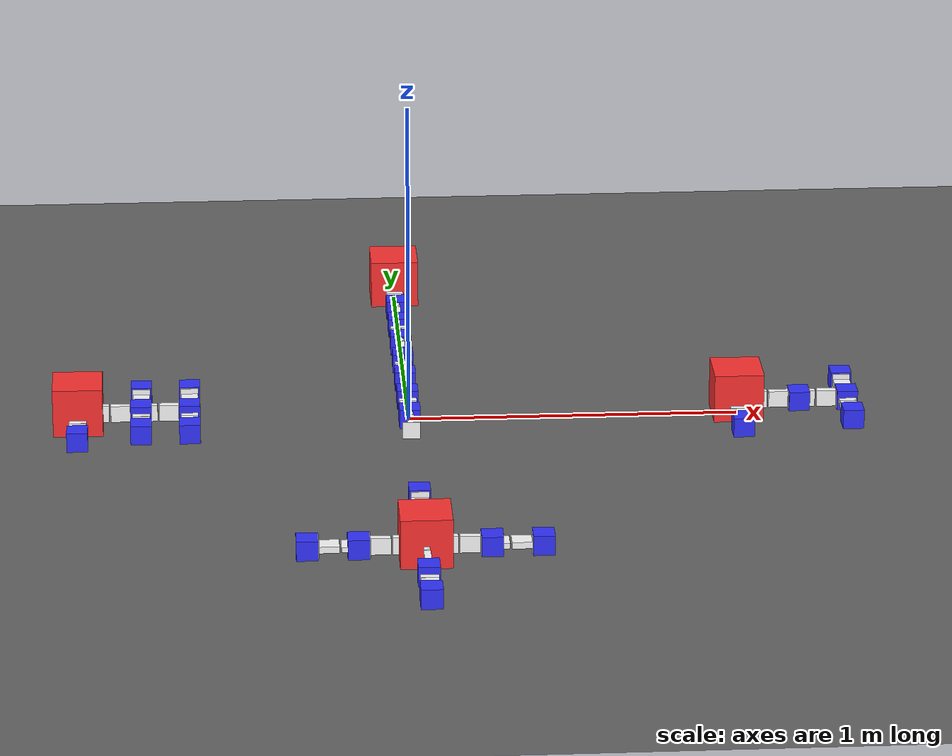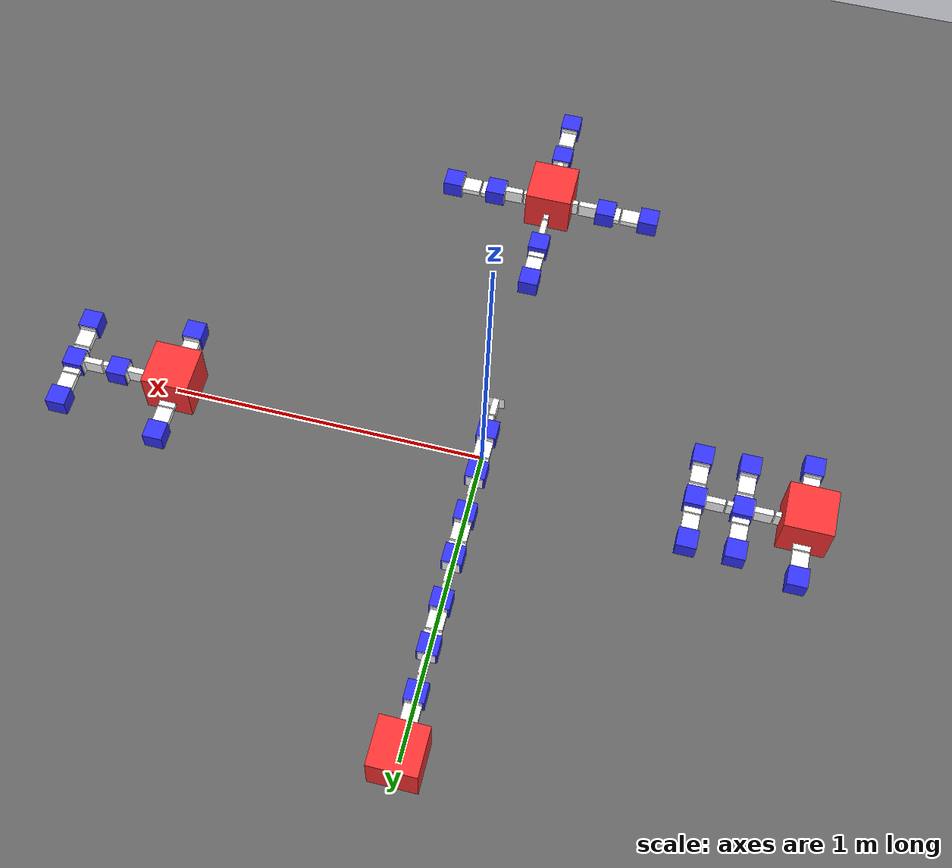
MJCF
<mujoco model="scene">
  <compiler autolimits="true" angle="radian"/>
  <option timestep="0.001" gravity="0 0 -9.8100000000000005" integrator="RK4"/>
  <visual>
    <headlight active="0"/>
  </visual>
  <default>
    <default class="/"/>
    <default class="mbs0/"/>
    <default class="mbs1/"/>
    <default class="mbs2/"/>
    <default class="mbs3/"/>
    <default class="mbs4/"/>
  </default>
  <asset>
    <material name="heightmap_0_material" class="/" texrepeat="1 1" emission="0" specular="0.5" shininess="0.5" reflectance="0" rgba="0.39215686274509803 0.39215686274509803 0.39215686274509803 1"/>
    <material name="mbs1/geom_mbs1_geom0_material" class="mbs1/" texrepeat="1 1" emission="0" specular="0.5" shininess="0.5" reflectance="0" rgba="1 0.19607843137254902 0.19607843137254902 1"/>
    <material name="mbs1/geom_mbs1_geom1_material" class="mbs1/" texrepeat="1 1" emission="0" specular="0.5" shininess="0.5" reflectance="0" rgba="1 1 1 1"/>
    <material name="mbs1/geom_mbs1_geom2_material" class="mbs1/" texrepeat="1 1" emission="0" specular="0.5" shininess="0.5" reflectance="0" rgba="1 1 1 1"/>
    <material name="mbs1/geom_mbs1_geom3_material" class="mbs1/" texrepeat="1 1" emission="0" specular="0.5" shininess="0.5" reflectance="0" rgba="1 1 1 1"/>
    <material name="mbs1/geom_mbs1_link0_geom0_material" class="mbs1/" texrepeat="1 1" emission="0" specular="0.5" shininess="0.5" reflectance="0" rgba="1 1 1 1"/>
    <material name="mbs1/geom_mbs1_link0_geom1_material" class="mbs1/" texrepeat="1 1" emission="0" specular="0.5" shininess="0.5" reflectance="0" rgba="1 1 1 1"/>
    <material name="mbs1/geom_mbs1_link0_geom2_material" class="mbs1/" texrepeat="1 1" emission="0" specular="0.5" shininess="0.5" reflectance="0" rgba="0.19607843137254902 0.19607843137254902 1 1"/>
    <material name="mbs1/geom_mbs1_link0_geom3_material" class="mbs1/" texrepeat="1 1" emission="0" specular="0.5" shininess="0.5" reflectance="0" rgba="1 1 1 1"/>
    <material name="mbs1/geom_mbs1_link0_link1_geom0_material" class="mbs1/" texrepeat="1 1" emission="0" specular="0.5" shininess="0.5" reflectance="0" rgba="1 1 1 1"/>
    <material name="mbs1/geom_mbs1_link0_link1_geom1_material" class="mbs1/" texrepeat="1 1" emission="0" specular="0.5" shininess="0.5" reflectance="0" rgba="1 1 1 1"/>
    <material name="mbs1/geom_mbs1_link0_link1_geom2_material" class="mbs1/" texrepeat="1 1" emission="0" specular="0.5" shininess="0.5" reflectance="0" rgba="0.19607843137254902 0.19607843137254902 1 1"/>
    <material name="mbs1/geom_mbs1_link0_link1_geom3_material" class="mbs1/" texrepeat="1 1" emission="0" specular="0.5" shininess="0.5" reflectance="0" rgba="1 1 1 1"/>
    <material name="mbs1/geom_mbs1_link0_link1_geom4_material" class="mbs1/" texrepeat="1 1" emission="0" specular="0.5" shininess="0.5" reflectance="0" rgba="1 1 1 1"/>
    <material name="mbs1/geom_mbs1_link0_link1_link1_geom0_material" class="mbs1/" texrepeat="1 1" emission="0" specular="0.5" shininess="0.5" reflectance="0" rgba="1 1 1 1"/>
    <material name="mbs1/geom_mbs1_link0_link1_link1_geom1_material" class="mbs1/" texrepeat="1 1" emission="0" specular="0.5" shininess="0.5" reflectance="0" rgba="1 1 1 1"/>
    <material name="mbs1/geom_mbs1_link0_link1_link1_geom2_material" class="mbs1/" texrepeat="1 1" emission="0" specular="0.5" shininess="0.5" reflectance="0" rgba="0.19607843137254902 0.19607843137254902 1 1"/>
    <material name="mbs1/geom_mbs1_link0_link1_link2_geom0_material" class="mbs1/" texrepeat="1 1" emission="0" specular="0.5" shininess="0.5" reflectance="0" rgba="1 1 1 1"/>
    <material name="mbs1/geom_mbs1_link0_link1_link2_geom1_material" class="mbs1/" texrepeat="1 1" emission="0" specular="0.5" shininess="0.5" reflectance="0" rgba="1 1 1 1"/>
    <material name="mbs1/geom_mbs1_link0_link1_link2_geom2_material" class="mbs1/" texrepeat="1 1" emission="0" specular="0.5" shininess="0.5" reflectance="0" rgba="0.19607843137254902 0.19607843137254902 1 1"/>
    <material name="mbs1/geom_mbs1_link1_geom0_material" class="mbs1/" texrepeat="1 1" emission="0" specular="0.5" shininess="0.5" reflectance="0" rgba="1 1 1 1"/>
    <material name="mbs1/geom_mbs1_link1_geom1_material" class="mbs1/" texrepeat="1 1" emission="0" specular="0.5" shininess="0.5" reflectance="0" rgba="1 1 1 1"/>
    <material name="mbs1/geom_mbs1_link1_geom2_material" class="mbs1/" texrepeat="1 1" emission="0" specular="0.5" shininess="0.5" reflectance="0" rgba="0.19607843137254902 0.19607843137254902 1 1"/>
    <material name="mbs1/geom_mbs1_link2_geom0_material" class="mbs1/" texrepeat="1 1" emission="0" specular="0.5" shininess="0.5" reflectance="0" rgba="1 1 1 1"/>
    <material name="mbs1/geom_mbs1_link2_geom1_material" class="mbs1/" texrepeat="1 1" emission="0" specular="0.5" shininess="0.5" reflectance="0" rgba="1 1 1 1"/>
    <material name="mbs1/geom_mbs1_link2_geom2_material" class="mbs1/" texrepeat="1 1" emission="0" specular="0.5" shininess="0.5" reflectance="0" rgba="0.19607843137254902 0.19607843137254902 1 1"/>
    <material name="mbs2/geom_mbs2_geom0_material" class="mbs2/" texrepeat="1 1" emission="0" specular="0.5" shininess="0.5" reflectance="0" rgba="1 0.19607843137254902 0.19607843137254902 1"/>
    <material name="mbs2/geom_mbs2_geom1_material" class="mbs2/" texrepeat="1 1" emission="0" specular="0.5" shininess="0.5" reflectance="0" rgba="1 1 1 1"/>
    <material name="mbs2/geom_mbs2_geom2_material" class="mbs2/" texrepeat="1 1" emission="0" specular="0.5" shininess="0.5" reflectance="0" rgba="1 1 1 1"/>
    <material name="mbs2/geom_mbs2_geom3_material" class="mbs2/" texrepeat="1 1" emission="0" specular="0.5" shininess="0.5" reflectance="0" rgba="1 1 1 1"/>
    <material name="mbs2/geom_mbs2_link0_geom0_material" class="mbs2/" texrepeat="1 1" emission="0" specular="0.5" shininess="0.5" reflectance="0" rgba="1 1 1 1"/>
    <material name="mbs2/geom_mbs2_link0_geom1_material" class="mbs2/" texrepeat="1 1" emission="0" specular="0.5" shininess="0.5" reflectance="0" rgba="1 1 1 1"/>
    <material name="mbs2/geom_mbs2_link0_geom2_material" class="mbs2/" texrepeat="1 1" emission="0" specular="0.5" shininess="0.5" reflectance="0" rgba="0.19607843137254902 0.19607843137254902 1 1"/>
    <material name="mbs2/geom_mbs2_link0_geom3_material" class="mbs2/" texrepeat="1 1" emission="0" specular="0.5" shininess="0.5" reflectance="0" rgba="1 1 1 1"/>
    <material name="mbs2/geom_mbs2_link0_geom4_material" class="mbs2/" texrepeat="1 1" emission="0" specular="0.5" shininess="0.5" reflectance="0" rgba="1 1 1 1"/>
    <material name="mbs2/geom_mbs2_link0_geom5_material" class="mbs2/" texrepeat="1 1" emission="0" specular="0.5" shininess="0.5" reflectance="0" rgba="1 1 1 1"/>
    <material name="mbs2/geom_mbs2_link0_link1_geom0_material" class="mbs2/" texrepeat="1 1" emission="0" specular="0.5" shininess="0.5" reflectance="0" rgba="1 1 1 1"/>
    <material name="mbs2/geom_mbs2_link0_link1_geom1_material" class="mbs2/" texrepeat="1 1" emission="0" specular="0.5" shininess="0.5" reflectance="0" rgba="1 1 1 1"/>
    <material name="mbs2/geom_mbs2_link0_link1_geom2_material" class="mbs2/" texrepeat="1 1" emission="0" specular="0.5" shininess="0.5" reflectance="0" rgba="0.19607843137254902 0.19607843137254902 1 1"/>
    <material name="mbs2/geom_mbs2_link0_link1_geom3_material" class="mbs2/" texrepeat="1 1" emission="0" specular="0.5" shininess="0.5" reflectance="0" rgba="1 1 1 1"/>
    <material name="mbs2/geom_mbs2_link0_link1_geom4_material" class="mbs2/" texrepeat="1 1" emission="0" specular="0.5" shininess="0.5" reflectance="0" rgba="1 1 1 1"/>
    <material name="mbs2/geom_mbs2_link0_link1_link1_geom0_material" class="mbs2/" texrepeat="1 1" emission="0" specular="0.5" shininess="0.5" reflectance="0" rgba="1 1 1 1"/>
    <material name="mbs2/geom_mbs2_link0_link1_link1_geom1_material" class="mbs2/" texrepeat="1 1" emission="0" specular="0.5" shininess="0.5" reflectance="0" rgba="1 1 1 1"/>
    <material name="mbs2/geom_mbs2_link0_link1_link1_geom2_material" class="mbs2/" texrepeat="1 1" emission="0" specular="0.5" shininess="0.5" reflectance="0" rgba="0.19607843137254902 0.19607843137254902 1 1"/>
    <material name="mbs2/geom_mbs2_link0_link1_link2_geom0_material" class="mbs2/" texrepeat="1 1" emission="0" specular="0.5" shininess="0.5" reflectance="0" rgba="1 1 1 1"/>
    <material name="mbs2/geom_mbs2_link0_link1_link2_geom1_material" class="mbs2/" texrepeat="1 1" emission="0" specular="0.5" shininess="0.5" reflectance="0" rgba="1 1 1 1"/>
    <material name="mbs2/geom_mbs2_link0_link1_link2_geom2_material" class="mbs2/" texrepeat="1 1" emission="0" specular="0.5" shininess="0.5" reflectance="0" rgba="0.19607843137254902 0.19607843137254902 1 1"/>
    <material name="mbs2/geom_mbs2_link0_link2_geom0_material" class="mbs2/" texrepeat="1 1" emission="0" specular="0.5" shininess="0.5" reflectance="0" rgba="1 1 1 1"/>
    <material name="mbs2/geom_mbs2_link0_link2_geom1_material" class="mbs2/" texrepeat="1 1" emission="0" specular="0.5" shininess="0.5" reflectance="0" rgba="1 1 1 1"/>
    <material name="mbs2/geom_mbs2_link0_link2_geom2_material" class="mbs2/" texrepeat="1 1" emission="0" specular="0.5" shininess="0.5" reflectance="0" rgba="0.19607843137254902 0.19607843137254902 1 1"/>
    <material name="mbs2/geom_mbs2_link0_link3_geom0_material" class="mbs2/" texrepeat="1 1" emission="0" specular="0.5" shininess="0.5" reflectance="0" rgba="1 1 1 1"/>
    <material name="mbs2/geom_mbs2_link0_link3_geom1_material" class="mbs2/" texrepeat="1 1" emission="0" specular="0.5" shininess="0.5" reflectance="0" rgba="1 1 1 1"/>
    <material name="mbs2/geom_mbs2_link0_link3_geom2_material" class="mbs2/" texrepeat="1 1" emission="0" specular="0.5" shininess="0.5" reflectance="0" rgba="0.19607843137254902 0.19607843137254902 1 1"/>
    <material name="mbs2/geom_mbs2_link1_geom0_material" class="mbs2/" texrepeat="1 1" emission="0" specular="0.5" shininess="0.5" reflectance="0" rgba="1 1 1 1"/>
    <material name="mbs2/geom_mbs2_link1_geom1_material" class="mbs2/" texrepeat="1 1" emission="0" specular="0.5" shininess="0.5" reflectance="0" rgba="1 1 1 1"/>
    <material name="mbs2/geom_mbs2_link1_geom2_material" class="mbs2/" texrepeat="1 1" emission="0" specular="0.5" shininess="0.5" reflectance="0" rgba="0.19607843137254902 0.19607843137254902 1 1"/>
    <material name="mbs2/geom_mbs2_link2_geom0_material" class="mbs2/" texrepeat="1 1" emission="0" specular="0.5" shininess="0.5" reflectance="0" rgba="1 1 1 1"/>
    <material name="mbs2/geom_mbs2_link2_geom1_material" class="mbs2/" texrepeat="1 1" emission="0" specular="0.5" shininess="0.5" reflectance="0" rgba="1 1 1 1"/>
    <material name="mbs2/geom_mbs2_link2_geom2_material" class="mbs2/" texrepeat="1 1" emission="0" specular="0.5" shininess="0.5" reflectance="0" rgba="0.19607843137254902 0.19607843137254902 1 1"/>
    <material name="mbs3/geom_mbs3_geom0_material" class="mbs3/" texrepeat="1 1" emission="0" specular="0.5" shininess="0.5" reflectance="0" rgba="1 0.19607843137254902 0.19607843137254902 1"/>
    <material name="mbs3/geom_mbs3_geom1_material" class="mbs3/" texrepeat="1 1" emission="0" specular="0.5" shininess="0.5" reflectance="0" rgba="1 1 1 1"/>
    <material name="mbs3/geom_mbs3_link0_geom0_material" class="mbs3/" texrepeat="1 1" emission="0" specular="0.5" shininess="0.5" reflectance="0" rgba="1 1 1 1"/>
    <material name="mbs3/geom_mbs3_link0_geom1_material" class="mbs3/" texrepeat="1 1" emission="0" specular="0.5" shininess="0.5" reflectance="0" rgba="1 1 1 1"/>
    <material name="mbs3/geom_mbs3_link0_geom2_material" class="mbs3/" texrepeat="1 1" emission="0" specular="0.5" shininess="0.5" reflectance="0" rgba="0.19607843137254902 0.19607843137254902 1 1"/>
    <material name="mbs3/geom_mbs3_link0_geom3_material" class="mbs3/" texrepeat="1 1" emission="0" specular="0.5" shininess="0.5" reflectance="0" rgba="1 1 1 1"/>
    <material name="mbs3/geom_mbs3_link0_link1_geom0_material" class="mbs3/" texrepeat="1 1" emission="0" specular="0.5" shininess="0.5" reflectance="0" rgba="1 1 1 1"/>
    <material name="mbs3/geom_mbs3_link0_link1_geom1_material" class="mbs3/" texrepeat="1 1" emission="0" specular="0.5" shininess="0.5" reflectance="0" rgba="1 1 1 1"/>
    <material name="mbs3/geom_mbs3_link0_link1_geom2_material" class="mbs3/" texrepeat="1 1" emission="0" specular="0.5" shininess="0.5" reflectance="0" rgba="0.19607843137254902 0.19607843137254902 1 1"/>
    <material name="mbs3/geom_mbs3_link0_link1_geom3_material" class="mbs3/" texrepeat="1 1" emission="0" specular="0.5" shininess="0.5" reflectance="0" rgba="1 1 1 1"/>
    <material name="mbs3/geom_mbs3_link0_link1_link1_geom0_material" class="mbs3/" texrepeat="1 1" emission="0" specular="0.5" shininess="0.5" reflectance="0" rgba="1 1 1 1"/>
    <material name="mbs3/geom_mbs3_link0_link1_link1_geom1_material" class="mbs3/" texrepeat="1 1" emission="0" specular="0.5" shininess="0.5" reflectance="0" rgba="1 1 1 1"/>
    <material name="mbs3/geom_mbs3_link0_link1_link1_geom2_material" class="mbs3/" texrepeat="1 1" emission="0" specular="0.5" shininess="0.5" reflectance="0" rgba="0.19607843137254902 0.19607843137254902 1 1"/>
    <material name="mbs3/geom_mbs3_link0_link1_link1_geom3_material" class="mbs3/" texrepeat="1 1" emission="0" specular="0.5" shininess="0.5" reflectance="0" rgba="1 1 1 1"/>
    <material name="mbs3/geom_mbs3_link0_link1_link1_link1_geom0_material" class="mbs3/" texrepeat="1 1" emission="0" specular="0.5" shininess="0.5" reflectance="0" rgba="1 1 1 1"/>
    <material name="mbs3/geom_mbs3_link0_link1_link1_link1_geom1_material" class="mbs3/" texrepeat="1 1" emission="0" specular="0.5" shininess="0.5" reflectance="0" rgba="1 1 1 1"/>
    <material name="mbs3/geom_mbs3_link0_link1_link1_link1_geom2_material" class="mbs3/" texrepeat="1 1" emission="0" specular="0.5" shininess="0.5" reflectance="0" rgba="0.19607843137254902 0.19607843137254902 1 1"/>
    <material name="mbs3/geom_mbs3_link0_link1_link1_link1_geom3_material" class="mbs3/" texrepeat="1 1" emission="0" specular="0.5" shininess="0.5" reflectance="0" rgba="1 1 1 1"/>
    <material name="mbs3/geom_mbs3_link0_link1_link1_link1_link1_geom0_material" class="mbs3/" texrepeat="1 1" emission="0" specular="0.5" shininess="0.5" reflectance="0" rgba="1 1 1 1"/>
    <material name="mbs3/geom_mbs3_link0_link1_link1_link1_link1_geom1_material" class="mbs3/" texrepeat="1 1" emission="0" specular="0.5" shininess="0.5" reflectance="0" rgba="1 1 1 1"/>
    <material name="mbs3/geom_mbs3_link0_link1_link1_link1_link1_geom2_material" class="mbs3/" texrepeat="1 1" emission="0" specular="0.5" shininess="0.5" reflectance="0" rgba="0.19607843137254902 0.19607843137254902 1 1"/>
    <material name="mbs3/geom_mbs3_link0_link1_link1_link1_link1_geom3_material" class="mbs3/" texrepeat="1 1" emission="0" specular="0.5" shininess="0.5" reflectance="0" rgba="1 1 1 1"/>
    <material name="mbs3/geom_mbs3_link0_link1_link1_link1_link1_link1_geom0_material" class="mbs3/" texrepeat="1 1" emission="0" specular="0.5" shininess="0.5" reflectance="0" rgba="1 1 1 1"/>
    <material name="mbs3/geom_mbs3_link0_link1_link1_link1_link1_link1_geom1_material" class="mbs3/" texrepeat="1 1" emission="0" specular="0.5" shininess="0.5" reflectance="0" rgba="1 1 1 1"/>
    <material name="mbs3/geom_mbs3_link0_link1_link1_link1_link1_link1_geom2_material" class="mbs3/" texrepeat="1 1" emission="0" specular="0.5" shininess="0.5" reflectance="0" rgba="0.19607843137254902 0.19607843137254902 1 1"/>
    <material name="mbs3/geom_mbs3_link0_link1_link1_link1_link1_link1_geom3_material" class="mbs3/" texrepeat="1 1" emission="0" specular="0.5" shininess="0.5" reflectance="0" rgba="1 1 1 1"/>
    <material name="mbs3/geom_mbs3_link0_link1_link1_link1_link1_link1_link1_geom0_material" class="mbs3/" texrepeat="1 1" emission="0" specular="0.5" shininess="0.5" reflectance="0" rgba="1 1 1 1"/>
    <material name="mbs3/geom_mbs3_link0_link1_link1_link1_link1_link1_link1_geom1_material" class="mbs3/" texrepeat="1 1" emission="0" specular="0.5" shininess="0.5" reflectance="0" rgba="1 1 1 1"/>
    <material name="mbs3/geom_mbs3_link0_link1_link1_link1_link1_link1_link1_geom2_material" class="mbs3/" texrepeat="1 1" emission="0" specular="0.5" shininess="0.5" reflectance="0" rgba="0.19607843137254902 0.19607843137254902 1 1"/>
    <material name="mbs3/geom_mbs3_link0_link1_link1_link1_link1_link1_link1_geom3_material" class="mbs3/" texrepeat="1 1" emission="0" specular="0.5" shininess="0.5" reflectance="0" rgba="1 1 1 1"/>
    <material name="mbs3/geom_mbs3_link0_link1_link1_link1_link1_link1_link1_link1_geom0_material" class="mbs3/" texrepeat="1 1" emission="0" specular="0.5" shininess="0.5" reflectance="0" rgba="1 1 1 1"/>
    <material name="mbs3/geom_mbs3_link0_link1_link1_link1_link1_link1_link1_link1_geom1_material" class="mbs3/" texrepeat="1 1" emission="0" specular="0.5" shininess="0.5" reflectance="0" rgba="1 1 1 1"/>
    <material name="mbs4/geom_mbs4_geom0_material" class="mbs4/" texrepeat="1 1" emission="0" specular="0.5" shininess="0.5" reflectance="0" rgba="1 0.19607843137254902 0.19607843137254902 1"/>
    <material name="mbs4/geom_mbs4_geom1_material" class="mbs4/" texrepeat="1 1" emission="0" specular="0.5" shininess="0.5" reflectance="0" rgba="1 1 1 1"/>
    <material name="mbs4/geom_mbs4_geom2_material" class="mbs4/" texrepeat="1 1" emission="0" specular="0.5" shininess="0.5" reflectance="0" rgba="1 1 1 1"/>
    <material name="mbs4/geom_mbs4_geom3_material" class="mbs4/" texrepeat="1 1" emission="0" specular="0.5" shininess="0.5" reflectance="0" rgba="1 1 1 1"/>
    <material name="mbs4/geom_mbs4_geom4_material" class="mbs4/" texrepeat="1 1" emission="0" specular="0.5" shininess="0.5" reflectance="0" rgba="1 1 1 1"/>
    <material name="mbs4/geom_mbs4_link0_geom0_material" class="mbs4/" texrepeat="1 1" emission="0" specular="0.5" shininess="0.5" reflectance="0" rgba="1 1 1 1"/>
    <material name="mbs4/geom_mbs4_link0_geom1_material" class="mbs4/" texrepeat="1 1" emission="0" specular="0.5" shininess="0.5" reflectance="0" rgba="1 1 1 1"/>
    <material name="mbs4/geom_mbs4_link0_geom2_material" class="mbs4/" texrepeat="1 1" emission="0" specular="0.5" shininess="0.5" reflectance="0" rgba="0.19607843137254902 0.19607843137254902 1 1"/>
    <material name="mbs4/geom_mbs4_link0_geom3_material" class="mbs4/" texrepeat="1 1" emission="0" specular="0.5" shininess="0.5" reflectance="0" rgba="1 1 1 1"/>
    <material name="mbs4/geom_mbs4_link0_link1_geom0_material" class="mbs4/" texrepeat="1 1" emission="0" specular="0.5" shininess="0.5" reflectance="0" rgba="1 1 1 1"/>
    <material name="mbs4/geom_mbs4_link0_link1_geom1_material" class="mbs4/" texrepeat="1 1" emission="0" specular="0.5" shininess="0.5" reflectance="0" rgba="1 1 1 1"/>
    <material name="mbs4/geom_mbs4_link0_link1_geom2_material" class="mbs4/" texrepeat="1 1" emission="0" specular="0.5" shininess="0.5" reflectance="0" rgba="0.19607843137254902 0.19607843137254902 1 1"/>
    <material name="mbs4/geom_mbs4_link1_geom0_material" class="mbs4/" texrepeat="1 1" emission="0" specular="0.5" shininess="0.5" reflectance="0" rgba="1 1 1 1"/>
    <material name="mbs4/geom_mbs4_link1_geom1_material" class="mbs4/" texrepeat="1 1" emission="0" specular="0.5" shininess="0.5" reflectance="0" rgba="1 1 1 1"/>
    <material name="mbs4/geom_mbs4_link1_geom2_material" class="mbs4/" texrepeat="1 1" emission="0" specular="0.5" shininess="0.5" reflectance="0" rgba="0.19607843137254902 0.19607843137254902 1 1"/>
    <material name="mbs4/geom_mbs4_link1_geom3_material" class="mbs4/" texrepeat="1 1" emission="0" specular="0.5" shininess="0.5" reflectance="0" rgba="1 1 1 1"/>
    <material name="mbs4/geom_mbs4_link1_link1_geom0_material" class="mbs4/" texrepeat="1 1" emission="0" specular="0.5" shininess="0.5" reflectance="0" rgba="1 1 1 1"/>
    <material name="mbs4/geom_mbs4_link1_link1_geom1_material" class="mbs4/" texrepeat="1 1" emission="0" specular="0.5" shininess="0.5" reflectance="0" rgba="1 1 1 1"/>
    <material name="mbs4/geom_mbs4_link1_link1_geom2_material" class="mbs4/" texrepeat="1 1" emission="0" specular="0.5" shininess="0.5" reflectance="0" rgba="0.19607843137254902 0.19607843137254902 1 1"/>
    <material name="mbs4/geom_mbs4_link2_geom0_material" class="mbs4/" texrepeat="1 1" emission="0" specular="0.5" shininess="0.5" reflectance="0" rgba="1 1 1 1"/>
    <material name="mbs4/geom_mbs4_link2_geom1_material" class="mbs4/" texrepeat="1 1" emission="0" specular="0.5" shininess="0.5" reflectance="0" rgba="1 1 1 1"/>
    <material name="mbs4/geom_mbs4_link2_geom2_material" class="mbs4/" texrepeat="1 1" emission="0" specular="0.5" shininess="0.5" reflectance="0" rgba="0.19607843137254902 0.19607843137254902 1 1"/>
    <material name="mbs4/geom_mbs4_link2_geom3_material" class="mbs4/" texrepeat="1 1" emission="0" specular="0.5" shininess="0.5" reflectance="0" rgba="1 1 1 1"/>
    <material name="mbs4/geom_mbs4_link2_link1_geom0_material" class="mbs4/" texrepeat="1 1" emission="0" specular="0.5" shininess="0.5" reflectance="0" rgba="1 1 1 1"/>
    <material name="mbs4/geom_mbs4_link2_link1_geom1_material" class="mbs4/" texrepeat="1 1" emission="0" specular="0.5" shininess="0.5" reflectance="0" rgba="1 1 1 1"/>
    <material name="mbs4/geom_mbs4_link2_link1_geom2_material" class="mbs4/" texrepeat="1 1" emission="0" specular="0.5" shininess="0.5" reflectance="0" rgba="0.19607843137254902 0.19607843137254902 1 1"/>
    <material name="mbs4/geom_mbs4_link3_geom0_material" class="mbs4/" texrepeat="1 1" emission="0" specular="0.5" shininess="0.5" reflectance="0" rgba="1 1 1 1"/>
    <material name="mbs4/geom_mbs4_link3_geom1_material" class="mbs4/" texrepeat="1 1" emission="0" specular="0.5" shininess="0.5" reflectance="0" rgba="1 1 1 1"/>
    <material name="mbs4/geom_mbs4_link3_geom2_material" class="mbs4/" texrepeat="1 1" emission="0" specular="0.5" shininess="0.5" reflectance="0" rgba="0.19607843137254902 0.19607843137254902 1 1"/>
    <material name="mbs4/geom_mbs4_link3_geom3_material" class="mbs4/" texrepeat="1 1" emission="0" specular="0.5" shininess="0.5" reflectance="0" rgba="1 1 1 1"/>
    <material name="mbs4/geom_mbs4_link3_link1_geom0_material" class="mbs4/" texrepeat="1 1" emission="0" specular="0.5" shininess="0.5" reflectance="0" rgba="1 1 1 1"/>
    <material name="mbs4/geom_mbs4_link3_link1_geom1_material" class="mbs4/" texrepeat="1 1" emission="0" specular="0.5" shininess="0.5" reflectance="0" rgba="1 1 1 1"/>
    <material name="mbs4/geom_mbs4_link3_link1_geom2_material" class="mbs4/" texrepeat="1 1" emission="0" specular="0.5" shininess="0.5" reflectance="0" rgba="0.19607843137254902 0.19607843137254902 1 1"/>
  </asset>
  <worldbody>
    <light name="//unnamed_light_0" class="/" directional="true" castshadow="false" pos="0 0 100" ambient="0.5 0.5 0.5"/>
    <body pos="0 0 0" quat="0 0 0 1" name="mbs0/"/>
    <geom name="//unnamed_geom_0" class="/" type="plane" size="10 10 1" material="heightmap_0_material" pos="0 0 0" quat="0 0 0 1"/>
    <body pos="1 0 0.074999999999999997" quat="0 0 0 1" name="mbs1/">
      <freejoint name="mbs1/"/>
      <geom name="mbs1/mbs1_geom0" class="mbs1/" type="box" size="0.074999999999999997 0.074999999999999997 0.074999999999999997" material="mbs1/geom_mbs1_geom0_material"/>
      <geom name="mbs1/mbs1_geom1" class="mbs1/" type="box" size="0.0089999999999999993 0.026499999999999999 0.0082945499999999995" material="mbs1/geom_mbs1_geom1_material" pos="-0.084000000000000005 0 -0.032000000000000001" quat="0 0 0.70710700000000004 0.70710700000000004"/>
      <geom name="mbs1/mbs1_geom2" class="mbs1/" type="box" size="0.0089999999999999993 0.026499999999999999 0.0082945499999999995" material="mbs1/geom_mbs1_geom2_material" pos="0 0.084000000000000005 -0.032000000000000001" quat="0.70710700000000004 0 0 0.70710700000000004"/>
      <geom name="mbs1/mbs1_geom3" class="mbs1/" type="box" size="0.0089999999999999993 0.026499999999999999 0.0082945499999999995" material="mbs1/geom_mbs1_geom3_material" pos="0 -0.084000000000000005 -0.032000000000000001" quat="0.70710700000000004 0 0 -0.70710700000000004"/>
      <body name="mbs1/mbs1_link0" pos="-0.109525 0 -0.032000000000000001" quat="0 0 0.70710700000000004 0.70710700000000004">
        <inertial pos="0.056922100000000003 0 0" quat="0 0.70710700000000004 0 0.70710700000000004" mass="0.15975" diaginertia="0.00026978499999999998 0.00025399800000000002 6.8728199999999997e-05"/>
        <joint name="mbs1/mbs1_joint0" class="mbs1/" pos="0 0 0" axis="0 1 0" range="-1.0471999999999999 1.0471999999999999" armature="0.002"/>
        <geom name="mbs1/mbs1_link0_geom0" class="mbs1/" type="box" size="0.029149999999999999 0.025600000000000001 0.01" material="mbs1/geom_mbs1_link0_geom0_material" pos="0.017999999999999999 0 0"/>
        <geom name="mbs1/mbs1_link0_geom1" class="mbs1/" type="box" size="0.001 0.026499999999999999 0.026499999999999999" material="mbs1/geom_mbs1_link0_geom1_material" pos="0.048149999999999998 0 0"/>
        <geom name="mbs1/mbs1_link0_geom2" class="mbs1/" type="box" size="0.031443100000000002 0.031443100000000002 0.03015" material="mbs1/geom_mbs1_link0_geom2_material" pos="0.080593100000000001 0 0" quat="0.70710700000000004 -0.70710700000000004 0 0"/>
        <geom name="mbs1/mbs1_link0_geom3" class="mbs1/" type="box" size="0.0089999999999999993 0.026499999999999999 0.0082945499999999995" material="mbs1/geom_mbs1_link0_geom3_material" pos="0.121036 0 0"/>
        <body name="mbs1/mbs1_link0_link1" pos="0.146561 0 0">
          <inertial pos="0.0553675 0 0" quat="0.5 0.5 0.5 0.5" mass="0.17607" diaginertia="0.00026573699999999999 0.000217932 0.00012644300000000001"/>
          <joint name="mbs1/mbs1_link0_joint1" class="mbs1/" pos="0 0 0" axis="0 1 0" range="-1.0471999999999999 1.0471999999999999" armature="0.002"/>
          <geom name="mbs1/mbs1_link0_link1_geom0" class="mbs1/" type="box" size="0.029149999999999999 0.025600000000000001 0.01" material="mbs1/geom_mbs1_link0_link1_geom0_material" pos="0.017999999999999999 0 0"/>
          <geom name="mbs1/mbs1_link0_link1_geom1" class="mbs1/" type="box" size="0.001 0.026499999999999999 0.026499999999999999" material="mbs1/geom_mbs1_link0_link1_geom1_material" pos="0.048149999999999998 0 0"/>
          <geom name="mbs1/mbs1_link0_link1_geom2" class="mbs1/" type="box" size="0.031443100000000002 0.031443100000000002 0.03015" material="mbs1/geom_mbs1_link0_link1_geom2_material" pos="0.080593100000000001 0 0" quat="0.70710700000000004 -0.70710700000000004 0 0"/>
          <geom name="mbs1/mbs1_link0_link1_geom3" class="mbs1/" type="box" size="0.0089999999999999993 0.026499999999999999 0.0082945499999999995" material="mbs1/geom_mbs1_link0_link1_geom3_material" pos="0.080593100000000001 0 -0.040443100000000003" quat="0.5 -0.5 0.5 0.5"/>
          <geom name="mbs1/mbs1_link0_link1_geom4" class="mbs1/" type="box" size="0.0089999999999999993 0.026499999999999999 0.0082945499999999995" material="mbs1/geom_mbs1_link0_link1_geom4_material" pos="0.080593100000000001 0 0.040443100000000003" quat="0.5 -0.5 -0.5 -0.5"/>
          <body name="mbs1/mbs1_link0_link1_link1" pos="0.080593100000000001 0 -0.065968100000000002" quat="0.5 -0.5 0.5 0.5">
            <inertial pos="0.049626900000000002 0 0" quat="0 0.70710700000000004 0 0.70710700000000004" mass="0.14343" diaginertia="0.000190805 0.000178464 6.4533699999999995e-05"/>
            <joint name="mbs1/mbs1_link0_link1_joint1" class="mbs1/" pos="0 0 0" axis="0 1 0" range="-1.0471999999999999 1.0471999999999999" armature="0.002"/>
            <geom name="mbs1/mbs1_link0_link1_link1_geom0" class="mbs1/" type="box" size="0.029149999999999999 0.025600000000000001 0.01" material="mbs1/geom_mbs1_link0_link1_link1_geom0_material" pos="0.017999999999999999 0 0"/>
            <geom name="mbs1/mbs1_link0_link1_link1_geom1" class="mbs1/" type="box" size="0.001 0.026499999999999999 0.026499999999999999" material="mbs1/geom_mbs1_link0_link1_link1_geom1_material" pos="0.048149999999999998 0 0"/>
            <geom name="mbs1/mbs1_link0_link1_link1_geom2" class="mbs1/" type="box" size="0.031443100000000002 0.031443100000000002 0.03015" material="mbs1/geom_mbs1_link0_link1_link1_geom2_material" pos="0.080593100000000001 0 0"/>
          </body>
          <body name="mbs1/mbs1_link0_link1_link2" pos="0.080593100000000001 0 0.065968100000000002" quat="0.5 -0.5 -0.5 -0.5">
            <inertial pos="0.049626900000000002 0 0" quat="0 0.70710700000000004 0 0.70710700000000004" mass="0.14343" diaginertia="0.000190805 0.000178464 6.4533699999999995e-05"/>
            <joint name="mbs1/mbs1_link0_link1_joint2" class="mbs1/" pos="0 0 0" axis="0 1 0" range="-1.0471999999999999 1.0471999999999999" armature="0.002"/>
            <geom name="mbs1/mbs1_link0_link1_link2_geom0" class="mbs1/" type="box" size="0.029149999999999999 0.025600000000000001 0.01" material="mbs1/geom_mbs1_link0_link1_link2_geom0_material" pos="0.017999999999999999 0 0"/>
            <geom name="mbs1/mbs1_link0_link1_link2_geom1" class="mbs1/" type="box" size="0.001 0.026499999999999999 0.026499999999999999" material="mbs1/geom_mbs1_link0_link1_link2_geom1_material" pos="0.048149999999999998 0 0"/>
            <geom name="mbs1/mbs1_link0_link1_link2_geom2" class="mbs1/" type="box" size="0.031443100000000002 0.031443100000000002 0.03015" material="mbs1/geom_mbs1_link0_link1_link2_geom2_material" pos="0.080593100000000001 0 0"/>
          </body>
        </body>
      </body>
      <body name="mbs1/mbs1_link1" pos="0 0.109525 -0.032000000000000001" quat="0.70710700000000004 0 0 0.70710700000000004">
        <inertial pos="0.049626900000000002 0 0" quat="0 0.70710700000000004 0 0.70710700000000004" mass="0.14343" diaginertia="0.000190805 0.000178464 6.4533699999999995e-05"/>
        <joint name="mbs1/mbs1_joint1" class="mbs1/" pos="0 0 0" axis="0 1 0" range="-1.0471999999999999 1.0471999999999999" armature="0.002"/>
        <geom name="mbs1/mbs1_link1_geom0" class="mbs1/" type="box" size="0.029149999999999999 0.025600000000000001 0.01" material="mbs1/geom_mbs1_link1_geom0_material" pos="0.017999999999999999 0 0"/>
        <geom name="mbs1/mbs1_link1_geom1" class="mbs1/" type="box" size="0.001 0.026499999999999999 0.026499999999999999" material="mbs1/geom_mbs1_link1_geom1_material" pos="0.048149999999999998 0 0"/>
        <geom name="mbs1/mbs1_link1_geom2" class="mbs1/" type="box" size="0.031443100000000002 0.031443100000000002 0.03015" material="mbs1/geom_mbs1_link1_geom2_material" pos="0.080593100000000001 0 0"/>
      </body>
      <body name="mbs1/mbs1_link2" pos="0 -0.109525 -0.032000000000000001" quat="0.70710700000000004 0 0 -0.70710700000000004">
        <inertial pos="0.049626900000000002 0 0" quat="0 0.70710700000000004 0 0.70710700000000004" mass="0.14343" diaginertia="0.000190805 0.000178464 6.4533699999999995e-05"/>
        <joint name="mbs1/mbs1_joint2" class="mbs1/" pos="0 0 0" axis="0 1 0" range="-1.0471999999999999 1.0471999999999999" armature="0.002"/>
        <geom name="mbs1/mbs1_link2_geom0" class="mbs1/" type="box" size="0.029149999999999999 0.025600000000000001 0.01" material="mbs1/geom_mbs1_link2_geom0_material" pos="0.017999999999999999 0 0"/>
        <geom name="mbs1/mbs1_link2_geom1" class="mbs1/" type="box" size="0.001 0.026499999999999999 0.026499999999999999" material="mbs1/geom_mbs1_link2_geom1_material" pos="0.048149999999999998 0 0"/>
        <geom name="mbs1/mbs1_link2_geom2" class="mbs1/" type="box" size="0.031443100000000002 0.031443100000000002 0.03015" material="mbs1/geom_mbs1_link2_geom2_material" pos="0.080593100000000001 0 0"/>
      </body>
    </body>
    <body pos="-1 0 0.074999999999999997" quat="0 0 0 1" name="mbs2/">
      <freejoint name="mbs2/"/>
      <geom name="mbs2/mbs2_geom0" class="mbs2/" type="box" size="0.074999999999999997 0.074999999999999997 0.074999999999999997" material="mbs2/geom_mbs2_geom0_material"/>
      <geom name="mbs2/mbs2_geom1" class="mbs2/" type="box" size="0.0089999999999999993 0.026499999999999999 0.0082945499999999995" material="mbs2/geom_mbs2_geom1_material" pos="-0.084000000000000005 0 -0.032000000000000001" quat="0 0 0.70710700000000004 0.70710700000000004"/>
      <geom name="mbs2/mbs2_geom2" class="mbs2/" type="box" size="0.0089999999999999993 0.026499999999999999 0.0082945499999999995" material="mbs2/geom_mbs2_geom2_material" pos="0 0.084000000000000005 -0.032000000000000001" quat="0.70710700000000004 0 0 0.70710700000000004"/>
      <geom name="mbs2/mbs2_geom3" class="mbs2/" type="box" size="0.0089999999999999993 0.026499999999999999 0.0082945499999999995" material="mbs2/geom_mbs2_geom3_material" pos="0 -0.084000000000000005 -0.032000000000000001" quat="0.70710700000000004 0 0 -0.70710700000000004"/>
      <body name="mbs2/mbs2_link0" pos="-0.109525 0 -0.032000000000000001" quat="0 0 0.70710700000000004 0.70710700000000004">
        <inertial pos="0.060937999999999999 0 0" quat="0.5 0.5 0.5 0.5" mass="0.19239000000000001" diaginertia="0.00033095999999999999 0.00028660099999999999 0.00013063699999999999"/>
        <joint name="mbs2/mbs2_joint0" class="mbs2/" pos="0 0 0" axis="0 1 0" range="-1.0471999999999999 1.0471999999999999" armature="0.002"/>
        <geom name="mbs2/mbs2_link0_geom0" class="mbs2/" type="box" size="0.029149999999999999 0.025600000000000001 0.01" material="mbs2/geom_mbs2_link0_geom0_material" pos="0.017999999999999999 0 0"/>
        <geom name="mbs2/mbs2_link0_geom1" class="mbs2/" type="box" size="0.001 0.026499999999999999 0.026499999999999999" material="mbs2/geom_mbs2_link0_geom1_material" pos="0.048149999999999998 0 0"/>
        <geom name="mbs2/mbs2_link0_geom2" class="mbs2/" type="box" size="0.031443100000000002 0.031443100000000002 0.03015" material="mbs2/geom_mbs2_link0_geom2_material" pos="0.080593100000000001 0 0" quat="0.70710700000000004 -0.70710700000000004 0 0"/>
        <geom name="mbs2/mbs2_link0_geom3" class="mbs2/" type="box" size="0.0089999999999999993 0.026499999999999999 0.0082945499999999995" material="mbs2/geom_mbs2_link0_geom3_material" pos="0.121036 0 0"/>
        <geom name="mbs2/mbs2_link0_geom4" class="mbs2/" type="box" size="0.0089999999999999993 0.026499999999999999 0.0082945499999999995" material="mbs2/geom_mbs2_link0_geom4_material" pos="0.080593100000000001 0 -0.040443100000000003" quat="0.5 -0.5 0.5 0.5"/>
        <geom name="mbs2/mbs2_link0_geom5" class="mbs2/" type="box" size="0.0089999999999999993 0.026499999999999999 0.0082945499999999995" material="mbs2/geom_mbs2_link0_geom5_material" pos="0.080593100000000001 0 0.040443100000000003" quat="0.5 -0.5 -0.5 -0.5"/>
        <body name="mbs2/mbs2_link0_link1" pos="0.146561 0 0">
          <inertial pos="0.0553675 0 0" quat="0.5 0.5 0.5 0.5" mass="0.17607" diaginertia="0.00026573699999999999 0.000217932 0.00012644300000000001"/>
          <joint name="mbs2/mbs2_link0_joint1" class="mbs2/" pos="0 0 0" axis="0 1 0" range="-1.0471999999999999 1.0471999999999999" armature="0.002"/>
          <geom name="mbs2/mbs2_link0_link1_geom0" class="mbs2/" type="box" size="0.029149999999999999 0.025600000000000001 0.01" material="mbs2/geom_mbs2_link0_link1_geom0_material" pos="0.017999999999999999 0 0"/>
          <geom name="mbs2/mbs2_link0_link1_geom1" class="mbs2/" type="box" size="0.001 0.026499999999999999 0.026499999999999999" material="mbs2/geom_mbs2_link0_link1_geom1_material" pos="0.048149999999999998 0 0"/>
          <geom name="mbs2/mbs2_link0_link1_geom2" class="mbs2/" type="box" size="0.031443100000000002 0.031443100000000002 0.03015" material="mbs2/geom_mbs2_link0_link1_geom2_material" pos="0.080593100000000001 0 0" quat="0.70710700000000004 -0.70710700000000004 0 0"/>
          <geom name="mbs2/mbs2_link0_link1_geom3" class="mbs2/" type="box" size="0.0089999999999999993 0.026499999999999999 0.0082945499999999995" material="mbs2/geom_mbs2_link0_link1_geom3_material" pos="0.080593100000000001 0 -0.040443100000000003" quat="0.5 -0.5 0.5 0.5"/>
          <geom name="mbs2/mbs2_link0_link1_geom4" class="mbs2/" type="box" size="0.0089999999999999993 0.026499999999999999 0.0082945499999999995" material="mbs2/geom_mbs2_link0_link1_geom4_material" pos="0.080593100000000001 0 0.040443100000000003" quat="0.5 -0.5 -0.5 -0.5"/>
          <body name="mbs2/mbs2_link0_link1_link1" pos="0.080593100000000001 0 -0.065968100000000002" quat="0.5 -0.5 0.5 0.5">
            <inertial pos="0.049626900000000002 0 0" quat="0 0.70710700000000004 0 0.70710700000000004" mass="0.14343" diaginertia="0.000190805 0.000178464 6.4533699999999995e-05"/>
            <joint name="mbs2/mbs2_link0_link1_joint1" class="mbs2/" pos="0 0 0" axis="0 1 0" range="-1.0471999999999999 1.0471999999999999" armature="0.002"/>
            <geom name="mbs2/mbs2_link0_link1_link1_geom0" class="mbs2/" type="box" size="0.029149999999999999 0.025600000000000001 0.01" material="mbs2/geom_mbs2_link0_link1_link1_geom0_material" pos="0.017999999999999999 0 0"/>
            <geom name="mbs2/mbs2_link0_link1_link1_geom1" class="mbs2/" type="box" size="0.001 0.026499999999999999 0.026499999999999999" material="mbs2/geom_mbs2_link0_link1_link1_geom1_material" pos="0.048149999999999998 0 0"/>
            <geom name="mbs2/mbs2_link0_link1_link1_geom2" class="mbs2/" type="box" size="0.031443100000000002 0.031443100000000002 0.03015" material="mbs2/geom_mbs2_link0_link1_link1_geom2_material" pos="0.080593100000000001 0 0"/>
          </body>
          <body name="mbs2/mbs2_link0_link1_link2" pos="0.080593100000000001 0 0.065968100000000002" quat="0.5 -0.5 -0.5 -0.5">
            <inertial pos="0.049626900000000002 0 0" quat="0 0.70710700000000004 0 0.70710700000000004" mass="0.14343" diaginertia="0.000190805 0.000178464 6.4533699999999995e-05"/>
            <joint name="mbs2/mbs2_link0_link1_joint2" class="mbs2/" pos="0 0 0" axis="0 1 0" range="-1.0471999999999999 1.0471999999999999" armature="0.002"/>
            <geom name="mbs2/mbs2_link0_link1_link2_geom0" class="mbs2/" type="box" size="0.029149999999999999 0.025600000000000001 0.01" material="mbs2/geom_mbs2_link0_link1_link2_geom0_material" pos="0.017999999999999999 0 0"/>
            <geom name="mbs2/mbs2_link0_link1_link2_geom1" class="mbs2/" type="box" size="0.001 0.026499999999999999 0.026499999999999999" material="mbs2/geom_mbs2_link0_link1_link2_geom1_material" pos="0.048149999999999998 0 0"/>
            <geom name="mbs2/mbs2_link0_link1_link2_geom2" class="mbs2/" type="box" size="0.031443100000000002 0.031443100000000002 0.03015" material="mbs2/geom_mbs2_link0_link1_link2_geom2_material" pos="0.080593100000000001 0 0"/>
          </body>
        </body>
        <body name="mbs2/mbs2_link0_link2" pos="0.080593100000000001 0 -0.065968100000000002" quat="0.5 -0.5 0.5 0.5">
          <inertial pos="0.049626900000000002 0 0" quat="0 0.70710700000000004 0 0.70710700000000004" mass="0.14343" diaginertia="0.000190805 0.000178464 6.4533699999999995e-05"/>
          <joint name="mbs2/mbs2_link0_joint2" class="mbs2/" pos="0 0 0" axis="0 1 0" range="-1.0471999999999999 1.0471999999999999" armature="0.002"/>
          <geom name="mbs2/mbs2_link0_link2_geom0" class="mbs2/" type="box" size="0.029149999999999999 0.025600000000000001 0.01" material="mbs2/geom_mbs2_link0_link2_geom0_material" pos="0.017999999999999999 0 0"/>
          <geom name="mbs2/mbs2_link0_link2_geom1" class="mbs2/" type="box" size="0.001 0.026499999999999999 0.026499999999999999" material="mbs2/geom_mbs2_link0_link2_geom1_material" pos="0.048149999999999998 0 0"/>
          <geom name="mbs2/mbs2_link0_link2_geom2" class="mbs2/" type="box" size="0.031443100000000002 0.031443100000000002 0.03015" material="mbs2/geom_mbs2_link0_link2_geom2_material" pos="0.080593100000000001 0 0"/>
        </body>
        <body name="mbs2/mbs2_link0_link3" pos="0.080593100000000001 0 0.065968100000000002" quat="0.5 -0.5 -0.5 -0.5">
          <inertial pos="0.049626900000000002 0 0" quat="0 0.70710700000000004 0 0.70710700000000004" mass="0.14343" diaginertia="0.000190805 0.000178464 6.4533699999999995e-05"/>
          <joint name="mbs2/mbs2_link0_joint3" class="mbs2/" pos="0 0 0" axis="0 1 0" range="-1.0471999999999999 1.0471999999999999" armature="0.002"/>
          <geom name="mbs2/mbs2_link0_link3_geom0" class="mbs2/" type="box" size="0.029149999999999999 0.025600000000000001 0.01" material="mbs2/geom_mbs2_link0_link3_geom0_material" pos="0.017999999999999999 0 0"/>
          <geom name="mbs2/mbs2_link0_link3_geom1" class="mbs2/" type="box" size="0.001 0.026499999999999999 0.026499999999999999" material="mbs2/geom_mbs2_link0_link3_geom1_material" pos="0.048149999999999998 0 0"/>
          <geom name="mbs2/mbs2_link0_link3_geom2" class="mbs2/" type="box" size="0.031443100000000002 0.031443100000000002 0.03015" material="mbs2/geom_mbs2_link0_link3_geom2_material" pos="0.080593100000000001 0 0"/>
        </body>
      </body>
      <body name="mbs2/mbs2_link1" pos="0 0.109525 -0.032000000000000001" quat="0.70710700000000004 0 0 0.70710700000000004">
        <inertial pos="0.049626900000000002 0 0" quat="0 0.70710700000000004 0 0.70710700000000004" mass="0.14343" diaginertia="0.000190805 0.000178464 6.4533699999999995e-05"/>
        <joint name="mbs2/mbs2_joint1" class="mbs2/" pos="0 0 0" axis="0 1 0" range="-1.0471999999999999 1.0471999999999999" armature="0.002"/>
        <geom name="mbs2/mbs2_link1_geom0" class="mbs2/" type="box" size="0.029149999999999999 0.025600000000000001 0.01" material="mbs2/geom_mbs2_link1_geom0_material" pos="0.017999999999999999 0 0"/>
        <geom name="mbs2/mbs2_link1_geom1" class="mbs2/" type="box" size="0.001 0.026499999999999999 0.026499999999999999" material="mbs2/geom_mbs2_link1_geom1_material" pos="0.048149999999999998 0 0"/>
        <geom name="mbs2/mbs2_link1_geom2" class="mbs2/" type="box" size="0.031443100000000002 0.031443100000000002 0.03015" material="mbs2/geom_mbs2_link1_geom2_material" pos="0.080593100000000001 0 0"/>
      </body>
      <body name="mbs2/mbs2_link2" pos="0 -0.109525 -0.032000000000000001" quat="0.70710700000000004 0 0 -0.70710700000000004">
        <inertial pos="0.049626900000000002 0 0" quat="0 0.70710700000000004 0 0.70710700000000004" mass="0.14343" diaginertia="0.000190805 0.000178464 6.4533699999999995e-05"/>
        <joint name="mbs2/mbs2_joint2" class="mbs2/" pos="0 0 0" axis="0 1 0" range="-1.0471999999999999 1.0471999999999999" armature="0.002"/>
        <geom name="mbs2/mbs2_link2_geom0" class="mbs2/" type="box" size="0.029149999999999999 0.025600000000000001 0.01" material="mbs2/geom_mbs2_link2_geom0_material" pos="0.017999999999999999 0 0"/>
        <geom name="mbs2/mbs2_link2_geom1" class="mbs2/" type="box" size="0.001 0.026499999999999999 0.026499999999999999" material="mbs2/geom_mbs2_link2_geom1_material" pos="0.048149999999999998 0 0"/>
        <geom name="mbs2/mbs2_link2_geom2" class="mbs2/" type="box" size="0.031443100000000002 0.031443100000000002 0.03015" material="mbs2/geom_mbs2_link2_geom2_material" pos="0.080593100000000001 0 0"/>
      </body>
    </body>
    <body pos="0 1 0.074999999999999997" quat="0 0 0 1" name="mbs3/">
      <freejoint name="mbs3/"/>
      <geom name="mbs3/mbs3_geom0" class="mbs3/" type="box" size="0.074999999999999997 0.074999999999999997 0.074999999999999997" material="mbs3/geom_mbs3_geom0_material"/>
      <geom name="mbs3/mbs3_geom1" class="mbs3/" type="box" size="0.0089999999999999993 0.026499999999999999 0.0082945499999999995" material="mbs3/geom_mbs3_geom1_material" pos="0 0.084000000000000005 -0.032000000000000001" quat="0.70710700000000004 0 0 0.70710700000000004"/>
      <body name="mbs3/mbs3_link0" pos="0 0.109525 -0.032000000000000001" quat="0.70710700000000004 0 0 0.70710700000000004">
        <inertial pos="0.056922100000000003 0 0" quat="0 0.70710700000000004 0 0.70710700000000004" mass="0.15975" diaginertia="0.00026978499999999998 0.00025737699999999999 6.53486e-05"/>
        <joint name="mbs3/mbs3_joint0" class="mbs3/" pos="0 0 0" axis="0 1 0" range="-1.0471999999999999 1.0471999999999999" armature="0.002"/>
        <geom name="mbs3/mbs3_link0_geom0" class="mbs3/" type="box" size="0.029149999999999999 0.025600000000000001 0.01" material="mbs3/geom_mbs3_link0_geom0_material" pos="0.017999999999999999 0 0"/>
        <geom name="mbs3/mbs3_link0_geom1" class="mbs3/" type="box" size="0.001 0.026499999999999999 0.026499999999999999" material="mbs3/geom_mbs3_link0_geom1_material" pos="0.048149999999999998 0 0"/>
        <geom name="mbs3/mbs3_link0_geom2" class="mbs3/" type="box" size="0.031443100000000002 0.031443100000000002 0.03015" material="mbs3/geom_mbs3_link0_geom2_material" pos="0.080593100000000001 0 0"/>
        <geom name="mbs3/mbs3_link0_geom3" class="mbs3/" type="box" size="0.0089999999999999993 0.026499999999999999 0.0082945499999999995" material="mbs3/geom_mbs3_link0_geom3_material" pos="0.121036 0 0" quat="0.70710700000000004 0.70710700000000004 0 0"/>
        <body name="mbs3/mbs3_link0_link1" pos="0.146561 0 0" quat="0.70710700000000004 0.70710700000000004 0 0">
          <inertial pos="0.056922100000000003 0 0" quat="0 0.70710700000000004 0 0.70710700000000004" mass="0.15975" diaginertia="0.00026978499999999998 0.00025737699999999999 6.53486e-05"/>
          <joint name="mbs3/mbs3_link0_joint1" class="mbs3/" pos="0 0 0" axis="0 1 0" range="-1.0471999999999999 1.0471999999999999" armature="0.002"/>
          <geom name="mbs3/mbs3_link0_link1_geom0" class="mbs3/" type="box" size="0.029149999999999999 0.025600000000000001 0.01" material="mbs3/geom_mbs3_link0_link1_geom0_material" pos="0.017999999999999999 0 0"/>
          <geom name="mbs3/mbs3_link0_link1_geom1" class="mbs3/" type="box" size="0.001 0.026499999999999999 0.026499999999999999" material="mbs3/geom_mbs3_link0_link1_geom1_material" pos="0.048149999999999998 0 0"/>
          <geom name="mbs3/mbs3_link0_link1_geom2" class="mbs3/" type="box" size="0.031443100000000002 0.031443100000000002 0.03015" material="mbs3/geom_mbs3_link0_link1_geom2_material" pos="0.080593100000000001 0 0" quat="0.70710700000000004 -0.70710700000000004 0 0"/>
          <geom name="mbs3/mbs3_link0_link1_geom3" class="mbs3/" type="box" size="0.0089999999999999993 0.026499999999999999 0.0082945499999999995" material="mbs3/geom_mbs3_link0_link1_geom3_material" pos="0.121036 0 0" quat="0.70710700000000004 -0.70710700000000004 0 0"/>
          <body name="mbs3/mbs3_link0_link1_link1" pos="0.146561 0 0" quat="0.70710700000000004 -0.70710700000000004 0 0">
            <inertial pos="0.056922100000000003 0 0" quat="0 0.70710700000000004 0 0.70710700000000004" mass="0.15975" diaginertia="0.00026978499999999998 0.00025737699999999999 6.53486e-05"/>
            <joint name="mbs3/mbs3_link0_link1_joint1" class="mbs3/" pos="0 0 0" axis="0 1 0" range="-1.0471999999999999 1.0471999999999999" armature="0.002"/>
            <geom name="mbs3/mbs3_link0_link1_link1_geom0" class="mbs3/" type="box" size="0.029149999999999999 0.025600000000000001 0.01" material="mbs3/geom_mbs3_link0_link1_link1_geom0_material" pos="0.017999999999999999 0 0"/>
            <geom name="mbs3/mbs3_link0_link1_link1_geom1" class="mbs3/" type="box" size="0.001 0.026499999999999999 0.026499999999999999" material="mbs3/geom_mbs3_link0_link1_link1_geom1_material" pos="0.048149999999999998 0 0"/>
            <geom name="mbs3/mbs3_link0_link1_link1_geom2" class="mbs3/" type="box" size="0.031443100000000002 0.031443100000000002 0.03015" material="mbs3/geom_mbs3_link0_link1_link1_geom2_material" pos="0.080593100000000001 0 0"/>
            <geom name="mbs3/mbs3_link0_link1_link1_geom3" class="mbs3/" type="box" size="0.0089999999999999993 0.026499999999999999 0.0082945499999999995" material="mbs3/geom_mbs3_link0_link1_link1_geom3_material" pos="0.121036 0 0" quat="0.70710700000000004 0.70710700000000004 0 0"/>
            <body name="mbs3/mbs3_link0_link1_link1_link1" pos="0.146561 0 0" quat="0.70710700000000004 0.70710700000000004 0 0">
              <inertial pos="0.056922100000000003 0 0" quat="0 0.70710700000000004 0 0.70710700000000004" mass="0.15975" diaginertia="0.00026978499999999998 0.00025737699999999999 6.53486e-05"/>
              <joint name="mbs3/mbs3_link0_link1_link1_joint1" class="mbs3/" pos="0 0 0" axis="0 1 0" range="-1.0471999999999999 1.0471999999999999" armature="0.002"/>
              <geom name="mbs3/mbs3_link0_link1_link1_link1_geom0" class="mbs3/" type="box" size="0.029149999999999999 0.025600000000000001 0.01" material="mbs3/geom_mbs3_link0_link1_link1_link1_geom0_material" pos="0.017999999999999999 0 0"/>
              <geom name="mbs3/mbs3_link0_link1_link1_link1_geom1" class="mbs3/" type="box" size="0.001 0.026499999999999999 0.026499999999999999" material="mbs3/geom_mbs3_link0_link1_link1_link1_geom1_material" pos="0.048149999999999998 0 0"/>
              <geom name="mbs3/mbs3_link0_link1_link1_link1_geom2" class="mbs3/" type="box" size="0.031443100000000002 0.031443100000000002 0.03015" material="mbs3/geom_mbs3_link0_link1_link1_link1_geom2_material" pos="0.080593100000000001 0 0" quat="0.70710700000000004 -0.70710700000000004 0 0"/>
              <geom name="mbs3/mbs3_link0_link1_link1_link1_geom3" class="mbs3/" type="box" size="0.0089999999999999993 0.026499999999999999 0.0082945499999999995" material="mbs3/geom_mbs3_link0_link1_link1_link1_geom3_material" pos="0.121036 0 0" quat="0.70710700000000004 -0.70710700000000004 0 0"/>
              <body name="mbs3/mbs3_link0_link1_link1_link1_link1" pos="0.146561 0 0" quat="0.70710700000000004 -0.70710700000000004 0 0">
                <inertial pos="0.056922100000000003 0 0" quat="0 0.70710700000000004 0 0.70710700000000004" mass="0.15975" diaginertia="0.00026978499999999998 0.00025737699999999999 6.53486e-05"/>
                <joint name="mbs3/mbs3_link0_link1_link1_link1_joint1" class="mbs3/" pos="0 0 0" axis="0 1 0" range="-1.0471999999999999 1.0471999999999999" armature="0.002"/>
                <geom name="mbs3/mbs3_link0_link1_link1_link1_link1_geom0" class="mbs3/" type="box" size="0.029149999999999999 0.025600000000000001 0.01" material="mbs3/geom_mbs3_link0_link1_link1_link1_link1_geom0_material" pos="0.017999999999999999 0 0"/>
                <geom name="mbs3/mbs3_link0_link1_link1_link1_link1_geom1" class="mbs3/" type="box" size="0.001 0.026499999999999999 0.026499999999999999" material="mbs3/geom_mbs3_link0_link1_link1_link1_link1_geom1_material" pos="0.048149999999999998 0 0"/>
                <geom name="mbs3/mbs3_link0_link1_link1_link1_link1_geom2" class="mbs3/" type="box" size="0.031443100000000002 0.031443100000000002 0.03015" material="mbs3/geom_mbs3_link0_link1_link1_link1_link1_geom2_material" pos="0.080593100000000001 0 0"/>
                <geom name="mbs3/mbs3_link0_link1_link1_link1_link1_geom3" class="mbs3/" type="box" size="0.0089999999999999993 0.026499999999999999 0.0082945499999999995" material="mbs3/geom_mbs3_link0_link1_link1_link1_link1_geom3_material" pos="0.121036 0 0" quat="0.70710700000000004 0.70710700000000004 0 0"/>
                <body name="mbs3/mbs3_link0_link1_link1_link1_link1_link1" pos="0.146561 0 0" quat="0.70710700000000004 0.70710700000000004 0 0">
                  <inertial pos="0.056922100000000003 0 0" quat="0 0.70710700000000004 0 0.70710700000000004" mass="0.15975" diaginertia="0.00026978499999999998 0.00025737699999999999 6.53486e-05"/>
                  <joint name="mbs3/mbs3_link0_link1_link1_link1_link1_joint1" class="mbs3/" pos="0 0 0" axis="0 1 0" range="-1.0471999999999999 1.0471999999999999" armature="0.002"/>
                  <geom name="mbs3/mbs3_link0_link1_link1_link1_link1_link1_geom0" class="mbs3/" type="box" size="0.029149999999999999 0.025600000000000001 0.01" material="mbs3/geom_mbs3_link0_link1_link1_link1_link1_link1_geom0_material" pos="0.017999999999999999 0 0"/>
                  <geom name="mbs3/mbs3_link0_link1_link1_link1_link1_link1_geom1" class="mbs3/" type="box" size="0.001 0.026499999999999999 0.026499999999999999" material="mbs3/geom_mbs3_link0_link1_link1_link1_link1_link1_geom1_material" pos="0.048149999999999998 0 0"/>
                  <geom name="mbs3/mbs3_link0_link1_link1_link1_link1_link1_geom2" class="mbs3/" type="box" size="0.031443100000000002 0.031443100000000002 0.03015" material="mbs3/geom_mbs3_link0_link1_link1_link1_link1_link1_geom2_material" pos="0.080593100000000001 0 0" quat="0.70710700000000004 -0.70710700000000004 0 0"/>
                  <geom name="mbs3/mbs3_link0_link1_link1_link1_link1_link1_geom3" class="mbs3/" type="box" size="0.0089999999999999993 0.026499999999999999 0.0082945499999999995" material="mbs3/geom_mbs3_link0_link1_link1_link1_link1_link1_geom3_material" pos="0.121036 0 0" quat="0.70710700000000004 -0.70710700000000004 0 0"/>
                  <body name="mbs3/mbs3_link0_link1_link1_link1_link1_link1_link1" pos="0.146561 0 0" quat="0.70710700000000004 -0.70710700000000004 0 0">
                    <inertial pos="0.056922100000000003 0 0" quat="0 0.70710700000000004 0 0.70710700000000004" mass="0.15975" diaginertia="0.00026978499999999998 0.00025737699999999999 6.53486e-05"/>
                    <joint name="mbs3/mbs3_link0_link1_link1_link1_link1_link1_joint1" class="mbs3/" pos="0 0 0" axis="0 1 0" range="-1.0471999999999999 1.0471999999999999" armature="0.002"/>
                    <geom name="mbs3/mbs3_link0_link1_link1_link1_link1_link1_link1_geom0" class="mbs3/" type="box" size="0.029149999999999999 0.025600000000000001 0.01" material="mbs3/geom_mbs3_link0_link1_link1_link1_link1_link1_link1_geom0_material" pos="0.017999999999999999 0 0"/>
                    <geom name="mbs3/mbs3_link0_link1_link1_link1_link1_link1_link1_geom1" class="mbs3/" type="box" size="0.001 0.026499999999999999 0.026499999999999999" material="mbs3/geom_mbs3_link0_link1_link1_link1_link1_link1_link1_geom1_material" pos="0.048149999999999998 0 0"/>
                    <geom name="mbs3/mbs3_link0_link1_link1_link1_link1_link1_link1_geom2" class="mbs3/" type="box" size="0.031443100000000002 0.031443100000000002 0.03015" material="mbs3/geom_mbs3_link0_link1_link1_link1_link1_link1_link1_geom2_material" pos="0.080593100000000001 0 0"/>
                    <geom name="mbs3/mbs3_link0_link1_link1_link1_link1_link1_link1_geom3" class="mbs3/" type="box" size="0.0089999999999999993 0.026499999999999999 0.0082945499999999995" material="mbs3/geom_mbs3_link0_link1_link1_link1_link1_link1_link1_geom3_material" pos="0.121036 0 0" quat="0.70710700000000004 0.70710700000000004 0 0"/>
                    <body name="mbs3/mbs3_link0_link1_link1_link1_link1_link1_link1_link1" pos="0.146561 0 0" quat="0.70710700000000004 0.70710700000000004 0 0">
                      <inertial pos="0.027081299999999999 0 0" quat="0 0.70710700000000004 0 0.70710700000000004" mass="0.083000000000000004" diaginertia="5.0839199999999999e-05 4.0102199999999997e-05 2.6307799999999999e-05"/>
                      <joint name="mbs3/mbs3_link0_link1_link1_link1_link1_link1_link1_joint1" class="mbs3/" pos="0 0 0" axis="0 1 0" range="-1.0471999999999999 1.0471999999999999" armature="0.002"/>
                      <geom name="mbs3/mbs3_link0_link1_link1_link1_link1_link1_link1_link1_geom0" class="mbs3/" type="box" size="0.029149999999999999 0.025600000000000001 0.01" material="mbs3/geom_mbs3_link0_link1_link1_link1_link1_link1_link1_link1_geom0_material" pos="0.017999999999999999 0 0"/>
                      <geom name="mbs3/mbs3_link0_link1_link1_link1_link1_link1_link1_link1_geom1" class="mbs3/" type="box" size="0.001 0.026499999999999999 0.026499999999999999" material="mbs3/geom_mbs3_link0_link1_link1_link1_link1_link1_link1_link1_geom1_material" pos="0.048149999999999998 0 0"/>
                    </body>
                  </body>
                </body>
              </body>
            </body>
          </body>
        </body>
      </body>
    </body>
    <body pos="0 -1 0.074999999999999997" quat="0 0 0 1" name="mbs4/">
      <freejoint name="mbs4/"/>
      <geom name="mbs4/mbs4_geom0" class="mbs4/" type="box" size="0.074999999999999997 0.074999999999999997 0.074999999999999997" material="mbs4/geom_mbs4_geom0_material"/>
      <geom name="mbs4/mbs4_geom1" class="mbs4/" type="box" size="0.0089999999999999993 0.026499999999999999 0.0082945499999999995" material="mbs4/geom_mbs4_geom1_material" pos="0.084000000000000005 0 -0.032000000000000001" quat="0.70710700000000004 0.70710700000000004 0 0"/>
      <geom name="mbs4/mbs4_geom2" class="mbs4/" type="box" size="0.0089999999999999993 0.026499999999999999 0.0082945499999999995" material="mbs4/geom_mbs4_geom2_material" pos="-0.084000000000000005 0 -0.032000000000000001" quat="0 0 0.70710700000000004 0.70710700000000004"/>
      <geom name="mbs4/mbs4_geom3" class="mbs4/" type="box" size="0.0089999999999999993 0.026499999999999999 0.0082945499999999995" material="mbs4/geom_mbs4_geom3_material" pos="0 0.084000000000000005 -0.032000000000000001" quat="0.5 0.5 0.5 0.5"/>
      <geom name="mbs4/mbs4_geom4" class="mbs4/" type="box" size="0.0089999999999999993 0.026499999999999999 0.0082945499999999995" material="mbs4/geom_mbs4_geom4_material" pos="0 -0.084000000000000005 -0.032000000000000001" quat="0.5 0.5 -0.5 -0.5"/>
      <body name="mbs4/mbs4_link0" pos="0.109525 0 -0.032000000000000001" quat="0.70710700000000004 0.70710700000000004 0 0">
        <inertial pos="0.056922100000000003 0 0" quat="0 0.70710700000000004 0 0.70710700000000004" mass="0.15975" diaginertia="0.00026978499999999998 0.00025737699999999999 6.53486e-05"/>
        <joint name="mbs4/mbs4_joint0" class="mbs4/" pos="0 0 0" axis="0 1 0" range="-1.0471999999999999 1.0471999999999999" armature="0.002"/>
        <geom name="mbs4/mbs4_link0_geom0" class="mbs4/" type="box" size="0.029149999999999999 0.025600000000000001 0.01" material="mbs4/geom_mbs4_link0_geom0_material" pos="0.017999999999999999 0 0"/>
        <geom name="mbs4/mbs4_link0_geom1" class="mbs4/" type="box" size="0.001 0.026499999999999999 0.026499999999999999" material="mbs4/geom_mbs4_link0_geom1_material" pos="0.048149999999999998 0 0"/>
        <geom name="mbs4/mbs4_link0_geom2" class="mbs4/" type="box" size="0.031443100000000002 0.031443100000000002 0.03015" material="mbs4/geom_mbs4_link0_geom2_material" pos="0.080593100000000001 0 0" quat="0.70710700000000004 -0.70710700000000004 0 0"/>
        <geom name="mbs4/mbs4_link0_geom3" class="mbs4/" type="box" size="0.0089999999999999993 0.026499999999999999 0.0082945499999999995" material="mbs4/geom_mbs4_link0_geom3_material" pos="0.121036 0 0" quat="0.70710700000000004 -0.70710700000000004 0 0"/>
        <body name="mbs4/mbs4_link0_link1" pos="0.146561 0 0" quat="0.70710700000000004 -0.70710700000000004 0 0">
          <inertial pos="0.049626900000000002 0 0" quat="0 0.70710700000000004 0 0.70710700000000004" mass="0.14343" diaginertia="0.000190805 0.000178464 6.4533699999999995e-05"/>
          <joint name="mbs4/mbs4_link0_joint1" class="mbs4/" pos="0 0 0" axis="0 1 0" range="-1.0471999999999999 1.0471999999999999" armature="0.002"/>
          <geom name="mbs4/mbs4_link0_link1_geom0" class="mbs4/" type="box" size="0.029149999999999999 0.025600000000000001 0.01" material="mbs4/geom_mbs4_link0_link1_geom0_material" pos="0.017999999999999999 0 0"/>
          <geom name="mbs4/mbs4_link0_link1_geom1" class="mbs4/" type="box" size="0.001 0.026499999999999999 0.026499999999999999" material="mbs4/geom_mbs4_link0_link1_geom1_material" pos="0.048149999999999998 0 0"/>
          <geom name="mbs4/mbs4_link0_link1_geom2" class="mbs4/" type="box" size="0.031443100000000002 0.031443100000000002 0.03015" material="mbs4/geom_mbs4_link0_link1_geom2_material" pos="0.080593100000000001 0 0"/>
        </body>
      </body>
      <body name="mbs4/mbs4_link1" pos="-0.109525 0 -0.032000000000000001" quat="0 0 0.70710700000000004 0.70710700000000004">
        <inertial pos="0.056922100000000003 0 0" quat="0 0.70710700000000004 0 0.70710700000000004" mass="0.15975" diaginertia="0.00026978499999999998 0.00025737699999999999 6.53486e-05"/>
        <joint name="mbs4/mbs4_joint1" class="mbs4/" pos="0 0 0" axis="0 1 0" range="-1.0471999999999999 1.0471999999999999" armature="0.002"/>
        <geom name="mbs4/mbs4_link1_geom0" class="mbs4/" type="box" size="0.029149999999999999 0.025600000000000001 0.01" material="mbs4/geom_mbs4_link1_geom0_material" pos="0.017999999999999999 0 0"/>
        <geom name="mbs4/mbs4_link1_geom1" class="mbs4/" type="box" size="0.001 0.026499999999999999 0.026499999999999999" material="mbs4/geom_mbs4_link1_geom1_material" pos="0.048149999999999998 0 0"/>
        <geom name="mbs4/mbs4_link1_geom2" class="mbs4/" type="box" size="0.031443100000000002 0.031443100000000002 0.03015" material="mbs4/geom_mbs4_link1_geom2_material" pos="0.080593100000000001 0 0" quat="0.70710700000000004 -0.70710700000000004 0 0"/>
        <geom name="mbs4/mbs4_link1_geom3" class="mbs4/" type="box" size="0.0089999999999999993 0.026499999999999999 0.0082945499999999995" material="mbs4/geom_mbs4_link1_geom3_material" pos="0.121036 0 0" quat="0.70710700000000004 -0.70710700000000004 0 0"/>
        <body name="mbs4/mbs4_link1_link1" pos="0.146561 0 0" quat="0.70710700000000004 -0.70710700000000004 0 0">
          <inertial pos="0.049626900000000002 0 0" quat="0 0.70710700000000004 0 0.70710700000000004" mass="0.14343" diaginertia="0.000190805 0.000178464 6.4533699999999995e-05"/>
          <joint name="mbs4/mbs4_link1_joint1" class="mbs4/" pos="0 0 0" axis="0 1 0" range="-1.0471999999999999 1.0471999999999999" armature="0.002"/>
          <geom name="mbs4/mbs4_link1_link1_geom0" class="mbs4/" type="box" size="0.029149999999999999 0.025600000000000001 0.01" material="mbs4/geom_mbs4_link1_link1_geom0_material" pos="0.017999999999999999 0 0"/>
          <geom name="mbs4/mbs4_link1_link1_geom1" class="mbs4/" type="box" size="0.001 0.026499999999999999 0.026499999999999999" material="mbs4/geom_mbs4_link1_link1_geom1_material" pos="0.048149999999999998 0 0"/>
          <geom name="mbs4/mbs4_link1_link1_geom2" class="mbs4/" type="box" size="0.031443100000000002 0.031443100000000002 0.03015" material="mbs4/geom_mbs4_link1_link1_geom2_material" pos="0.080593100000000001 0 0"/>
        </body>
      </body>
      <body name="mbs4/mbs4_link2" pos="0 0.109525 -0.032000000000000001" quat="0.5 0.5 0.5 0.5">
        <inertial pos="0.056922100000000003 0 0" quat="0 0.70710700000000004 0 0.70710700000000004" mass="0.15975" diaginertia="0.00026978499999999998 0.00025737699999999999 6.53486e-05"/>
        <joint name="mbs4/mbs4_joint2" class="mbs4/" pos="0 0 0" axis="0 1 0" range="-1.0471999999999999 1.0471999999999999" armature="0.002"/>
        <geom name="mbs4/mbs4_link2_geom0" class="mbs4/" type="box" size="0.029149999999999999 0.025600000000000001 0.01" material="mbs4/geom_mbs4_link2_geom0_material" pos="0.017999999999999999 0 0"/>
        <geom name="mbs4/mbs4_link2_geom1" class="mbs4/" type="box" size="0.001 0.026499999999999999 0.026499999999999999" material="mbs4/geom_mbs4_link2_geom1_material" pos="0.048149999999999998 0 0"/>
        <geom name="mbs4/mbs4_link2_geom2" class="mbs4/" type="box" size="0.031443100000000002 0.031443100000000002 0.03015" material="mbs4/geom_mbs4_link2_geom2_material" pos="0.080593100000000001 0 0" quat="0.70710700000000004 -0.70710700000000004 0 0"/>
        <geom name="mbs4/mbs4_link2_geom3" class="mbs4/" type="box" size="0.0089999999999999993 0.026499999999999999 0.0082945499999999995" material="mbs4/geom_mbs4_link2_geom3_material" pos="0.121036 0 0" quat="0.70710700000000004 -0.70710700000000004 0 0"/>
        <body name="mbs4/mbs4_link2_link1" pos="0.146561 0 0" quat="0.70710700000000004 -0.70710700000000004 0 0">
          <inertial pos="0.049626900000000002 0 0" quat="0 0.70710700000000004 0 0.70710700000000004" mass="0.14343" diaginertia="0.000190805 0.000178464 6.4533699999999995e-05"/>
          <joint name="mbs4/mbs4_link2_joint1" class="mbs4/" pos="0 0 0" axis="0 1 0" range="-1.0471999999999999 1.0471999999999999" armature="0.002"/>
          <geom name="mbs4/mbs4_link2_link1_geom0" class="mbs4/" type="box" size="0.029149999999999999 0.025600000000000001 0.01" material="mbs4/geom_mbs4_link2_link1_geom0_material" pos="0.017999999999999999 0 0"/>
          <geom name="mbs4/mbs4_link2_link1_geom1" class="mbs4/" type="box" size="0.001 0.026499999999999999 0.026499999999999999" material="mbs4/geom_mbs4_link2_link1_geom1_material" pos="0.048149999999999998 0 0"/>
          <geom name="mbs4/mbs4_link2_link1_geom2" class="mbs4/" type="box" size="0.031443100000000002 0.031443100000000002 0.03015" material="mbs4/geom_mbs4_link2_link1_geom2_material" pos="0.080593100000000001 0 0"/>
        </body>
      </body>
      <body name="mbs4/mbs4_link3" pos="0 -0.109525 -0.032000000000000001" quat="0.5 0.5 -0.5 -0.5">
        <inertial pos="0.056922100000000003 0 0" quat="0 0.70710700000000004 0 0.70710700000000004" mass="0.15975" diaginertia="0.00026978499999999998 0.00025737699999999999 6.53486e-05"/>
        <joint name="mbs4/mbs4_joint3" class="mbs4/" pos="0 0 0" axis="0 1 0" range="-1.0471999999999999 1.0471999999999999" armature="0.002"/>
        <geom name="mbs4/mbs4_link3_geom0" class="mbs4/" type="box" size="0.029149999999999999 0.025600000000000001 0.01" material="mbs4/geom_mbs4_link3_geom0_material" pos="0.017999999999999999 0 0"/>
        <geom name="mbs4/mbs4_link3_geom1" class="mbs4/" type="box" size="0.001 0.026499999999999999 0.026499999999999999" material="mbs4/geom_mbs4_link3_geom1_material" pos="0.048149999999999998 0 0"/>
        <geom name="mbs4/mbs4_link3_geom2" class="mbs4/" type="box" size="0.031443100000000002 0.031443100000000002 0.03015" material="mbs4/geom_mbs4_link3_geom2_material" pos="0.080593100000000001 0 0" quat="0.70710700000000004 -0.70710700000000004 0 0"/>
        <geom name="mbs4/mbs4_link3_geom3" class="mbs4/" type="box" size="0.0089999999999999993 0.026499999999999999 0.0082945499999999995" material="mbs4/geom_mbs4_link3_geom3_material" pos="0.121036 0 0" quat="0.70710700000000004 -0.70710700000000004 0 0"/>
        <body name="mbs4/mbs4_link3_link1" pos="0.146561 0 0" quat="0.70710700000000004 -0.70710700000000004 0 0">
          <inertial pos="0.049626900000000002 0 0" quat="0 0.70710700000000004 0 0.70710700000000004" mass="0.14343" diaginertia="0.000190805 0.000178464 6.4533699999999995e-05"/>
          <joint name="mbs4/mbs4_link3_joint1" class="mbs4/" pos="0 0 0" axis="0 1 0" range="-1.0471999999999999 1.0471999999999999" armature="0.002"/>
          <geom name="mbs4/mbs4_link3_link1_geom0" class="mbs4/" type="box" size="0.029149999999999999 0.025600000000000001 0.01" material="mbs4/geom_mbs4_link3_link1_geom0_material" pos="0.017999999999999999 0 0"/>
          <geom name="mbs4/mbs4_link3_link1_geom1" class="mbs4/" type="box" size="0.001 0.026499999999999999 0.026499999999999999" material="mbs4/geom_mbs4_link3_link1_geom1_material" pos="0.048149999999999998 0 0"/>
          <geom name="mbs4/mbs4_link3_link1_geom2" class="mbs4/" type="box" size="0.031443100000000002 0.031443100000000002 0.03015" material="mbs4/geom_mbs4_link3_link1_geom2_material" pos="0.080593100000000001 0 0"/>
        </body>
      </body>
    </body>
  </worldbody>
  <actuator>
    <position name="mbs1/actuator_position_mbs1_joint0" class="mbs1/" joint="mbs1/mbs1_joint0" kp="5"/>
    <velocity name="mbs1/actuator_velocity_mbs1_joint0" class="mbs1/" joint="mbs1/mbs1_joint0" kv="0.050000000000000003"/>
    <position name="mbs1/actuator_position_mbs1_link0_joint1" class="mbs1/" joint="mbs1/mbs1_link0_joint1" kp="5"/>
    <velocity name="mbs1/actuator_velocity_mbs1_link0_joint1" class="mbs1/" joint="mbs1/mbs1_link0_joint1" kv="0.050000000000000003"/>
    <position name="mbs1/actuator_position_mbs1_link0_link1_joint1" class="mbs1/" joint="mbs1/mbs1_link0_link1_joint1" kp="5"/>
    <velocity name="mbs1/actuator_velocity_mbs1_link0_link1_joint1" class="mbs1/" joint="mbs1/mbs1_link0_link1_joint1" kv="0.050000000000000003"/>
    <position name="mbs1/actuator_position_mbs1_link0_link1_joint2" class="mbs1/" joint="mbs1/mbs1_link0_link1_joint2" kp="5"/>
    <velocity name="mbs1/actuator_velocity_mbs1_link0_link1_joint2" class="mbs1/" joint="mbs1/mbs1_link0_link1_joint2" kv="0.050000000000000003"/>
    <position name="mbs1/actuator_position_mbs1_joint1" class="mbs1/" joint="mbs1/mbs1_joint1" kp="5"/>
    <velocity name="mbs1/actuator_velocity_mbs1_joint1" class="mbs1/" joint="mbs1/mbs1_joint1" kv="0.050000000000000003"/>
    <position name="mbs1/actuator_position_mbs1_joint2" class="mbs1/" joint="mbs1/mbs1_joint2" kp="5"/>
    <velocity name="mbs1/actuator_velocity_mbs1_joint2" class="mbs1/" joint="mbs1/mbs1_joint2" kv="0.050000000000000003"/>
    <position name="mbs2/actuator_position_mbs2_joint0" class="mbs2/" joint="mbs2/mbs2_joint0" kp="5"/>
    <velocity name="mbs2/actuator_velocity_mbs2_joint0" class="mbs2/" joint="mbs2/mbs2_joint0" kv="0.050000000000000003"/>
    <position name="mbs2/actuator_position_mbs2_link0_joint1" class="mbs2/" joint="mbs2/mbs2_link0_joint1" kp="5"/>
    <velocity name="mbs2/actuator_velocity_mbs2_link0_joint1" class="mbs2/" joint="mbs2/mbs2_link0_joint1" kv="0.050000000000000003"/>
    <position name="mbs2/actuator_position_mbs2_link0_link1_joint1" class="mbs2/" joint="mbs2/mbs2_link0_link1_joint1" kp="5"/>
    <velocity name="mbs2/actuator_velocity_mbs2_link0_link1_joint1" class="mbs2/" joint="mbs2/mbs2_link0_link1_joint1" kv="0.050000000000000003"/>
    <position name="mbs2/actuator_position_mbs2_link0_link1_joint2" class="mbs2/" joint="mbs2/mbs2_link0_link1_joint2" kp="5"/>
    <velocity name="mbs2/actuator_velocity_mbs2_link0_link1_joint2" class="mbs2/" joint="mbs2/mbs2_link0_link1_joint2" kv="0.050000000000000003"/>
    <position name="mbs2/actuator_position_mbs2_link0_joint2" class="mbs2/" joint="mbs2/mbs2_link0_joint2" kp="5"/>
    <velocity name="mbs2/actuator_velocity_mbs2_link0_joint2" class="mbs2/" joint="mbs2/mbs2_link0_joint2" kv="0.050000000000000003"/>
    <position name="mbs2/actuator_position_mbs2_link0_joint3" class="mbs2/" joint="mbs2/mbs2_link0_joint3" kp="5"/>
    <velocity name="mbs2/actuator_velocity_mbs2_link0_joint3" class="mbs2/" joint="mbs2/mbs2_link0_joint3" kv="0.050000000000000003"/>
    <position name="mbs2/actuator_position_mbs2_joint1" class="mbs2/" joint="mbs2/mbs2_joint1" kp="5"/>
    <velocity name="mbs2/actuator_velocity_mbs2_joint1" class="mbs2/" joint="mbs2/mbs2_joint1" kv="0.050000000000000003"/>
    <position name="mbs2/actuator_position_mbs2_joint2" class="mbs2/" joint="mbs2/mbs2_joint2" kp="5"/>
    <velocity name="mbs2/actuator_velocity_mbs2_joint2" class="mbs2/" joint="mbs2/mbs2_joint2" kv="0.050000000000000003"/>
    <position name="mbs3/actuator_position_mbs3_joint0" class="mbs3/" joint="mbs3/mbs3_joint0" kp="5"/>
    <velocity name="mbs3/actuator_velocity_mbs3_joint0" class="mbs3/" joint="mbs3/mbs3_joint0" kv="0.050000000000000003"/>
    <position name="mbs3/actuator_position_mbs3_link0_joint1" class="mbs3/" joint="mbs3/mbs3_link0_joint1" kp="5"/>
    <velocity name="mbs3/actuator_velocity_mbs3_link0_joint1" class="mbs3/" joint="mbs3/mbs3_link0_joint1" kv="0.050000000000000003"/>
    <position name="mbs3/actuator_position_mbs3_link0_link1_joint1" class="mbs3/" joint="mbs3/mbs3_link0_link1_joint1" kp="5"/>
    <velocity name="mbs3/actuator_velocity_mbs3_link0_link1_joint1" class="mbs3/" joint="mbs3/mbs3_link0_link1_joint1" kv="0.050000000000000003"/>
    <position name="mbs3/actuator_position_mbs3_link0_link1_link1_joint1" class="mbs3/" joint="mbs3/mbs3_link0_link1_link1_joint1" kp="5"/>
    <velocity name="mbs3/actuator_velocity_mbs3_link0_link1_link1_joint1" class="mbs3/" joint="mbs3/mbs3_link0_link1_link1_joint1" kv="0.050000000000000003"/>
    <position name="mbs3/actuator_position_mbs3_link0_link1_link1_link1_joint1" class="mbs3/" joint="mbs3/mbs3_link0_link1_link1_link1_joint1" kp="5"/>
    <velocity name="mbs3/actuator_velocity_mbs3_link0_link1_link1_link1_joint1" class="mbs3/" joint="mbs3/mbs3_link0_link1_link1_link1_joint1" kv="0.050000000000000003"/>
    <position name="mbs3/actuator_position_mbs3_link0_link1_link1_link1_link1_joint1" class="mbs3/" joint="mbs3/mbs3_link0_link1_link1_link1_link1_joint1" kp="5"/>
    <velocity name="mbs3/actuator_velocity_mbs3_link0_link1_link1_link1_link1_joint1" class="mbs3/" joint="mbs3/mbs3_link0_link1_link1_link1_link1_joint1" kv="0.050000000000000003"/>
    <position name="mbs3/actuator_position_mbs3_link0_link1_link1_link1_link1_link1_joint1" class="mbs3/" joint="mbs3/mbs3_link0_link1_link1_link1_link1_link1_joint1" kp="5"/>
    <velocity name="mbs3/actuator_velocity_mbs3_link0_link1_link1_link1_link1_link1_joint1" class="mbs3/" joint="mbs3/mbs3_link0_link1_link1_link1_link1_link1_joint1" kv="0.050000000000000003"/>
    <position name="mbs3/actuator_position_mbs3_link0_link1_link1_link1_link1_link1_link1_joint1" class="mbs3/" joint="mbs3/mbs3_link0_link1_link1_link1_link1_link1_link1_joint1" kp="5"/>
    <velocity name="mbs3/actuator_velocity_mbs3_link0_link1_link1_link1_link1_link1_link1_joint1" class="mbs3/" joint="mbs3/mbs3_link0_link1_link1_link1_link1_link1_link1_joint1" kv="0.050000000000000003"/>
    <position name="mbs4/actuator_position_mbs4_joint0" class="mbs4/" joint="mbs4/mbs4_joint0" kp="5"/>
    <velocity name="mbs4/actuator_velocity_mbs4_joint0" class="mbs4/" joint="mbs4/mbs4_joint0" kv="0.050000000000000003"/>
    <position name="mbs4/actuator_position_mbs4_link0_joint1" class="mbs4/" joint="mbs4/mbs4_link0_joint1" kp="5"/>
    <velocity name="mbs4/actuator_velocity_mbs4_link0_joint1" class="mbs4/" joint="mbs4/mbs4_link0_joint1" kv="0.050000000000000003"/>
    <position name="mbs4/actuator_position_mbs4_joint1" class="mbs4/" joint="mbs4/mbs4_joint1" kp="5"/>
    <velocity name="mbs4/actuator_velocity_mbs4_joint1" class="mbs4/" joint="mbs4/mbs4_joint1" kv="0.050000000000000003"/>
    <position name="mbs4/actuator_position_mbs4_link1_joint1" class="mbs4/" joint="mbs4/mbs4_link1_joint1" kp="5"/>
    <velocity name="mbs4/actuator_velocity_mbs4_link1_joint1" class="mbs4/" joint="mbs4/mbs4_link1_joint1" kv="0.050000000000000003"/>
    <position name="mbs4/actuator_position_mbs4_joint2" class="mbs4/" joint="mbs4/mbs4_joint2" kp="5"/>
    <velocity name="mbs4/actuator_velocity_mbs4_joint2" class="mbs4/" joint="mbs4/mbs4_joint2" kv="0.050000000000000003"/>
    <position name="mbs4/actuator_position_mbs4_link2_joint1" class="mbs4/" joint="mbs4/mbs4_link2_joint1" kp="5"/>
    <velocity name="mbs4/actuator_velocity_mbs4_link2_joint1" class="mbs4/" joint="mbs4/mbs4_link2_joint1" kv="0.050000000000000003"/>
    <position name="mbs4/actuator_position_mbs4_joint3" class="mbs4/" joint="mbs4/mbs4_joint3" kp="5"/>
    <velocity name="mbs4/actuator_velocity_mbs4_joint3" class="mbs4/" joint="mbs4/mbs4_joint3" kv="0.050000000000000003"/>
    <position name="mbs4/actuator_position_mbs4_link3_joint1" class="mbs4/" joint="mbs4/mbs4_link3_joint1" kp="5"/>
    <velocity name="mbs4/actuator_velocity_mbs4_link3_joint1" class="mbs4/" joint="mbs4/mbs4_link3_joint1" kv="0.050000000000000003"/>
  </actuator>
</mujoco>
